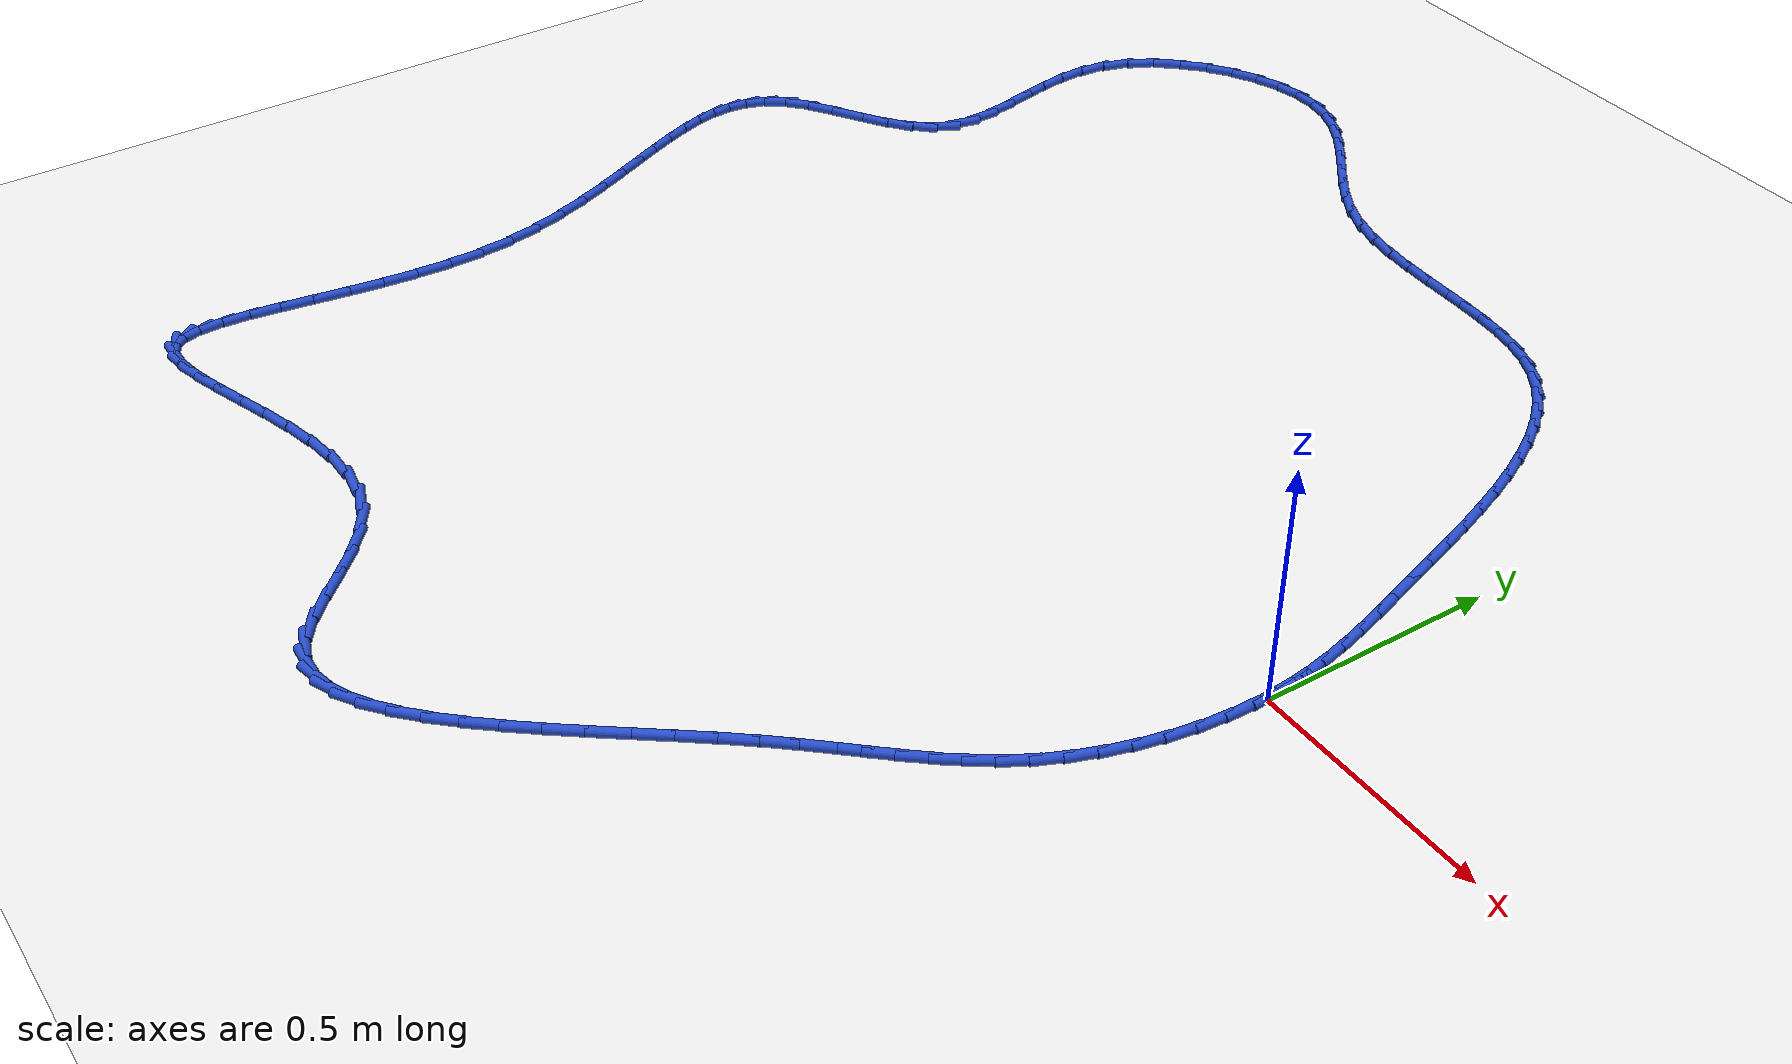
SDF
<sdf version="1.6">
 <world name="default">
  <light name="sun" type="directional">
   <pose>0 0 10 0 -0 0</pose>
   <diffuse>0.8 0.8 0.8 1</diffuse>
   <specular>0.2 0.2 0.2 1</specular>
   <attenuation>
    <range>1000</range>
    <constant>0.9</constant>
    <linear>0.01</linear>
    <quadratic>0.001</quadratic>
   </attenuation>
   <direction>-0.5 0.1 -0.9</direction>
  </light>
  <model name="ground_plane">
   <static>1</static>
   <link name="link">
    <collision name="collision">
     <geometry><plane><normal>0 0 1</normal><size>100 100</size></plane></geometry>
     <surface><friction><ode><mu>100</mu><mu2>50</mu2></ode></friction></surface>
    </collision>
    <visual name="visual">
     <cast_shadows>0</cast_shadows>
     <geometry><plane><normal>0 0 1</normal><size>100 100</size></plane></geometry>
     <material>
      <script><uri>file://media/materials/scripts/gazebo.material</uri><name>Gazebo/WhiteGlow</name></script>
     </material>
    </visual>
   </link>
  </model>
  <gravity>0 0 -9.8</gravity>
  <magnetic_field>6e-06 2.3e-05 -4.2e-05</magnetic_field>
  <atmosphere type="adiabatic"/>
  <physics name="default_physics" default="0" type="ode">
   <max_step_size>0.001</max_step_size>
   <real_time_factor>1</real_time_factor>
   <real_time_update_rate>1000</real_time_update_rate>
  </physics>
  <scene><ambient>0.4 0.4 0.4 1</ambient><background>0.7 0.7 0.7 1</background><shadows>1</shadows></scene>
  <spherical_coordinates>
   <surface_model>EARTH_WGS84</surface_model>
   <latitude_deg>0</latitude_deg>
   <longitude_deg>0</longitude_deg>
   <elevation>0</elevation>
   <heading_deg>0</heading_deg>
  </spherical_coordinates>
  <model name="line">
   <link name="link_0">
    <pose>4.5102810375396984e-17 -6.938893903907228e-17 0.01 0 1.57 -1.5004712339174642</pose>
    <collision name="collision">
     <geometry><cylinder><radius>0.01</radius><length>0.08</length></cylinder></geometry>
    </collision>
    <visual name="visual">
     <material>
      <script><name>Gazebo/Blue</name><uri>file://media/materials/scripts/gazebo.material</uri></script>
     </material>
     <geometry><cylinder><radius>0.01</radius><length>0.08</length></cylinder></geometry>
    </visual>
   </link>
   <link name="link_1">
    <pose>-0.004037575416281745 0.05731833337059254 0.01 0 1.57 -1.4348186650927535</pose>
    <collision name="collision">
     <geometry><cylinder><radius>0.01</radius><length>0.08</length></cylinder></geometry>
    </collision>
    <visual name="visual">
     <material>
      <script><name>Gazebo/Blue</name><uri>file://media/materials/scripts/gazebo.material</uri></script>
     </material>
     <geometry><cylinder><radius>0.01</radius><length>0.08</length></cylinder></geometry>
    </visual>
   </link>
   <link name="link_2">
    <pose>-0.01175211621200765 0.11370211652022898 0.01 0 1.57 -1.3787049932847433</pose>
    <collision name="collision">
     <geometry><cylinder><radius>0.01</radius><length>0.08</length></cylinder></geometry>
    </collision>
    <visual name="visual">
     <material>
      <script><name>Gazebo/Blue</name><uri>file://media/materials/scripts/gazebo.material</uri></script>
     </material>
     <geometry><cylinder><radius>0.01</radius><length>0.08</length></cylinder></geometry>
    </visual>
   </link>
   <link name="link_3">
    <pose>-0.022615047114090035 0.1695557052910629 0.01 0 1.57 -1.3334182568257678</pose>
    <collision name="collision">
     <geometry><cylinder><radius>0.01</radius><length>0.08</length></cylinder></geometry>
    </collision>
    <visual name="visual">
     <material>
      <script><name>Gazebo/Blue</name><uri>file://media/materials/scripts/gazebo.material</uri></script>
     </material>
     <geometry><cylinder><radius>0.01</radius><length>0.08</length></cylinder></geometry>
    </visual>
   </link>
   <link name="link_4">
    <pose>-0.03609779284944128 0.22528345552524812 0.01 0 1.57 -1.2995728628402556</pose>
    <collision name="collision">
     <geometry><cylinder><radius>0.01</radius><length>0.08</length></cylinder></geometry>
    </collision>
    <visual name="visual">
     <material>
      <script><name>Gazebo/Blue</name><uri>file://media/materials/scripts/gazebo.material</uri></script>
     </material>
     <geometry><cylinder><radius>0.01</radius><length>0.08</length></cylinder></geometry>
    </visual>
   </link>
   <link name="link_5">
    <pose>-0.05167177814497375 0.28128972306493855 0.01 0 1.57 -1.2772384988308771</pose>
    <collision name="collision">
     <geometry><cylinder><radius>0.01</radius><length>0.08</length></cylinder></geometry>
    </collision>
    <visual name="visual">
     <material>
      <script><name>Gazebo/Blue</name><uri>file://media/materials/scripts/gazebo.material</uri></script>
     </material>
     <geometry><cylinder><radius>0.01</radius><length>0.08</length></cylinder></geometry>
    </visual>
   </link>
   <link name="link_6">
    <pose>-0.06880842772759982 0.3379788637522878 0.01 0 1.57 -1.2660893254949797</pose>
    <collision name="collision">
     <geometry><cylinder><radius>0.01</radius><length>0.08</length></cylinder></geometry>
    </collision>
    <visual name="visual">
     <material>
      <script><name>Gazebo/Blue</name><uri>file://media/materials/scripts/gazebo.material</uri></script>
     </material>
     <geometry><cylinder><radius>0.01</radius><length>0.08</length></cylinder></geometry>
    </visual>
   </link>
   <link name="link_7">
    <pose>-0.08697916632423186 0.39575523342944985 0.01 0 1.57 -1.2653944081947126</pose>
    <collision name="collision">
     <geometry><cylinder><radius>0.01</radius><length>0.08</length></cylinder></geometry>
    </collision>
    <visual name="visual">
     <material>
      <script><name>Gazebo/Blue</name><uri>file://media/materials/scripts/gazebo.material</uri></script>
     </material>
     <geometry><cylinder><radius>0.01</radius><length>0.08</length></cylinder></geometry>
    </visual>
   </link>
   <link name="link_8">
    <pose>-0.10566166746171395 0.45501490058101823 0.01 0 1.57 -1.267503994169695</pose>
    <collision name="collision">
     <geometry><cylinder><radius>0.01</radius><length>0.08</length></cylinder></geometry>
    </collision>
    <visual name="visual">
     <material>
      <script><name>Gazebo/Blue</name><uri>file://media/materials/scripts/gazebo.material</uri></script>
     </material>
     <geometry><cylinder><radius>0.01</radius><length>0.08</length></cylinder></geometry>
    </visual>
   </link>
   <link name="link_9">
    <pose>-0.12465964398622445 0.5157215299584679 0.01 0 1.57 -1.2622437780268578</pose>
    <collision name="collision">
     <geometry><cylinder><radius>0.01</radius><length>0.08</length></cylinder></geometry>
    </collision>
    <visual name="visual">
     <material>
      <script><name>Gazebo/Blue</name><uri>file://media/materials/scripts/gazebo.material</uri></script>
     </material>
     <geometry><cylinder><radius>0.01</radius><length>0.08</length></cylinder></geometry>
    </visual>
   </link>
   <link name="link_10">
    <pose>-0.1442559000347422 0.5772034001792652 0.01 0 1.57 -1.2489859484521901</pose>
    <collision name="collision">
     <geometry><cylinder><radius>0.01</radius><length>0.08</length></cylinder></geometry>
    </collision>
    <visual name="visual">
     <material>
      <script><name>Gazebo/Blue</name><uri>file://media/materials/scripts/gazebo.material</uri></script>
     </material>
     <geometry><cylinder><radius>0.01</radius><length>0.08</length></cylinder></geometry>
    </visual>
   </link>
   <link name="link_11">
    <pose>-0.16477152747685883 0.6387380114500136 0.01 0 1.57 -1.2275007552103896</pose>
    <collision name="collision">
     <geometry><cylinder><radius>0.01</radius><length>0.08</length></cylinder></geometry>
    </collision>
    <visual name="visual">
     <material>
      <script><name>Gazebo/Blue</name><uri>file://media/materials/scripts/gazebo.material</uri></script>
     </material>
     <geometry><cylinder><radius>0.01</radius><length>0.08</length></cylinder></geometry>
    </visual>
   </link>
   <link name="link_12">
    <pose>-0.18652761818216598 0.6996028639773169 0.01 0 1.57 -1.1971415014831155</pose>
    <collision name="collision">
     <geometry><cylinder><radius>0.01</radius><length>0.08</length></cylinder></geometry>
    </collision>
    <visual name="visual">
     <material>
      <script><name>Gazebo/Blue</name><uri>file://media/materials/scripts/gazebo.material</uri></script>
     </material>
     <geometry><cylinder><radius>0.01</radius><length>0.08</length></cylinder></geometry>
    </visual>
   </link>
   <link name="link_13">
    <pose>-0.20984526402025536 0.7590754579677793 0.01 0 1.57 -1.156832286936047</pose>
    <collision name="collision">
     <geometry><cylinder><radius>0.01</radius><length>0.08</length></cylinder></geometry>
    </collision>
    <visual name="visual">
     <material>
      <script><name>Gazebo/Blue</name><uri>file://media/materials/scripts/gazebo.material</uri></script>
     </material>
     <geometry><cylinder><radius>0.01</radius><length>0.08</length></cylinder></geometry>
    </visual>
   </link>
   <link name="link_14">
    <pose>-0.2350455568607184 0.8164332936280038 0.01 0 1.57 -1.1050417511093311</pose>
    <collision name="collision">
     <geometry><cylinder><radius>0.01</radius><length>0.08</length></cylinder></geometry>
    </collision>
    <visual name="visual">
     <material>
      <script><name>Gazebo/Blue</name><uri>file://media/materials/scripts/gazebo.material</uri></script>
     </material>
     <geometry><cylinder><radius>0.01</radius><length>0.08</length></cylinder></geometry>
    </visual>
   </link>
   <link name="link_15">
    <pose>-0.2624495885731468 0.8709538711645946 0.01 0 1.57 -1.039773630951853</pose>
    <collision name="collision">
     <geometry><cylinder><radius>0.01</radius><length>0.08</length></cylinder></geometry>
    </collision>
    <visual name="visual">
     <material>
      <script><name>Gazebo/Blue</name><uri>file://media/materials/scripts/gazebo.material</uri></script>
     </material>
     <geometry><cylinder><radius>0.01</radius><length>0.08</length></cylinder></geometry>
    </visual>
   </link>
   <link name="link_16">
    <pose>-0.2923784510271322 0.9219146907841551 0.01 0 1.57 -0.9586370048366245</pose>
    <collision name="collision">
     <geometry><cylinder><radius>0.01</radius><length>0.08</length></cylinder></geometry>
    </collision>
    <visual name="visual">
     <material>
      <script><name>Gazebo/Blue</name><uri>file://media/materials/scripts/gazebo.material</uri></script>
     </material>
     <geometry><cylinder><radius>0.01</radius><length>0.08</length></cylinder></geometry>
    </visual>
   </link>
   <link name="link_17">
    <pose>-0.3251532360922663 0.9685932526932897 0.01 0 1.57 -0.8591155314883006</pose>
    <collision name="collision">
     <geometry><cylinder><radius>0.01</radius><length>0.08</length></cylinder></geometry>
    </collision>
    <visual name="visual">
     <material>
      <script><name>Gazebo/Blue</name><uri>file://media/materials/scripts/gazebo.material</uri></script>
     </material>
     <geometry><cylinder><radius>0.01</radius><length>0.08</length></cylinder></geometry>
    </visual>
   </link>
   <link name="link_18">
    <pose>-0.3610950356381406 1.0102670570986017 0.01 0 1.57 -0.7392181946435298</pose>
    <collision name="collision">
     <geometry><cylinder><radius>0.01</radius><length>0.08</length></cylinder></geometry>
    </collision>
    <visual name="visual">
     <material>
      <script><name>Gazebo/Blue</name><uri>file://media/materials/scripts/gazebo.material</uri></script>
     </material>
     <geometry><cylinder><radius>0.01</radius><length>0.08</length></cylinder></geometry>
    </visual>
   </link>
   <link name="link_19">
    <pose>-0.40052494153434676 1.0462136042066947 0.01 0 1.57 -0.598664868687921</pose>
    <collision name="collision">
     <geometry><cylinder><radius>0.01</radius><length>0.08</length></cylinder></geometry>
    </collision>
    <visual name="visual">
     <material>
      <script><name>Gazebo/Blue</name><uri>file://media/materials/scripts/gazebo.material</uri></script>
     </material>
     <geometry><cylinder><radius>0.01</radius><length>0.08</length></cylinder></geometry>
    </visual>
   </link>
   <link name="link_20">
    <pose>-0.44376404565047645 1.0757103942241728 0.01 0 1.57 -0.44076989092278057</pose>
    <collision name="collision">
     <geometry><cylinder><radius>0.01</radius><length>0.08</length></cylinder></geometry>
    </collision>
    <visual name="visual">
     <material>
      <script><name>Gazebo/Blue</name><uri>file://media/materials/scripts/gazebo.material</uri></script>
     </material>
     <geometry><cylinder><radius>0.01</radius><length>0.08</length></cylinder></geometry>
    </visual>
   </link>
   <link name="link_21">
    <pose>-0.49112551370021873 1.0980518119375509 0.01 0 1.57 -0.28991057319260055</pose>
    <collision name="collision">
     <geometry><cylinder><radius>0.01</radius><length>0.08</length></cylinder></geometry>
    </collision>
    <visual name="visual">
     <material>
      <script><name>Gazebo/Blue</name><uri>file://media/materials/scripts/gazebo.material</uri></script>
     </material>
     <geometry><cylinder><radius>0.01</radius><length>0.08</length></cylinder></geometry>
    </visual>
   </link>
   <link name="link_22">
    <pose>-0.5425225149336386 1.113384328862062 0.01 0 1.57 -0.17540187897770868</pose>
    <collision name="collision">
     <geometry><cylinder><radius>0.01</radius><length>0.08</length></cylinder></geometry>
    </collision>
    <visual name="visual">
     <material>
      <script><name>Gazebo/Blue</name><uri>file://media/materials/scripts/gazebo.material</uri></script>
     </material>
     <geometry><cylinder><radius>0.01</radius><length>0.08</length></cylinder></geometry>
    </visual>
   </link>
   <link name="link_23">
    <pose>-0.5972881653668255 1.1230900665937942 0.01 0 1.57 -0.09649198751842684</pose>
    <collision name="collision">
     <geometry><cylinder><radius>0.01</radius><length>0.08</length></cylinder></geometry>
    </collision>
    <visual name="visual">
     <material>
      <script><name>Gazebo/Blue</name><uri>file://media/materials/scripts/gazebo.material</uri></script>
     </material>
     <geometry><cylinder><radius>0.01</radius><length>0.08</length></cylinder></geometry>
    </visual>
   </link>
   <link name="link_24">
    <pose>-0.6547100768377834 1.1286480813514521 0.01 0 1.57 -0.04863188194610277</pose>
    <collision name="collision">
     <geometry><cylinder><radius>0.01</radius><length>0.08</length></cylinder></geometry>
    </collision>
    <visual name="visual">
     <material>
      <script><name>Gazebo/Blue</name><uri>file://media/materials/scripts/gazebo.material</uri></script>
     </material>
     <geometry><cylinder><radius>0.01</radius><length>0.08</length></cylinder></geometry>
    </visual>
   </link>
   <link name="link_25">
    <pose>-0.7140758611845153 1.1315374293537401 0.01 0 1.57 -0.02804238416598587</pose>
    <collision name="collision">
     <geometry><cylinder><radius>0.01</radius><length>0.08</length></cylinder></geometry>
    </collision>
    <visual name="visual">
     <material>
      <script><name>Gazebo/Blue</name><uri>file://media/materials/scripts/gazebo.material</uri></script>
     </material>
     <geometry><cylinder><radius>0.01</radius><length>0.08</length></cylinder></geometry>
    </visual>
   </link>
   <link name="link_26">
    <pose>-0.7746731302450247 1.1332371668193626 0.01 0 1.57 -0.03253598554440818</pose>
    <collision name="collision">
     <geometry><cylinder><radius>0.01</radius><length>0.08</length></cylinder></geometry>
    </collision>
    <visual name="visual">
     <material>
      <script><name>Gazebo/Blue</name><uri>file://media/materials/scripts/gazebo.material</uri></script>
     </material>
     <geometry><cylinder><radius>0.01</radius><length>0.08</length></cylinder></geometry>
    </visual>
   </link>
   <link name="link_27">
    <pose>-0.8357894958573145 1.1352263499670232 0.01 0 1.57 -0.061601138990094215</pose>
    <collision name="collision">
     <geometry><cylinder><radius>0.01</radius><length>0.08</length></cylinder></geometry>
    </collision>
    <visual name="visual">
     <material>
      <script><name>Gazebo/Blue</name><uri>file://media/materials/scripts/gazebo.material</uri></script>
     </material>
     <geometry><cylinder><radius>0.01</radius><length>0.08</length></cylinder></geometry>
    </visual>
   </link>
   <link name="link_28">
    <pose>-0.896712569859389 1.1389840350154266 0.01 0 1.57 -0.11619445598043322</pose>
    <collision name="collision">
     <geometry><cylinder><radius>0.01</radius><length>0.08</length></cylinder></geometry>
    </collision>
    <visual name="visual">
     <material>
      <script><name>Gazebo/Blue</name><uri>file://media/materials/scripts/gazebo.material</uri></script>
     </material>
     <geometry><cylinder><radius>0.01</radius><length>0.08</length></cylinder></geometry>
    </visual>
   </link>
   <link name="link_29">
    <pose>-0.9567299640892505 1.145989278183276 0.01 0 1.57 -0.19825145970880895</pose>
    <collision name="collision">
     <geometry><cylinder><radius>0.01</radius><length>0.08</length></cylinder></geometry>
    </collision>
    <visual name="visual">
     <material>
      <script><name>Gazebo/Blue</name><uri>file://media/materials/scripts/gazebo.material</uri></script>
     </material>
     <geometry><cylinder><radius>0.01</radius><length>0.08</length></cylinder></geometry>
    </visual>
   </link>
   <link name="link_30">
    <pose>-1.0151292903849032 1.1577211356892771 0.01 0 1.57 -0.3096299711926921</pose>
    <collision name="collision">
     <geometry><cylinder><radius>0.01</radius><length>0.08</length></cylinder></geometry>
    </collision>
    <visual name="visual">
     <material>
      <script><name>Gazebo/Blue</name><uri>file://media/materials/scripts/gazebo.material</uri></script>
     </material>
     <geometry><cylinder><radius>0.01</radius><length>0.08</length></cylinder></geometry>
    </visual>
   </link>
   <link name="link_31">
    <pose>-1.0711981605843497 1.1756586637521331 0.01 0 1.57 -0.44812639900255224</pose>
    <collision name="collision">
     <geometry><cylinder><radius>0.01</radius><length>0.08</length></cylinder></geometry>
    </collision>
    <visual name="visual">
     <material>
      <script><name>Gazebo/Blue</name><uri>file://media/materials/scripts/gazebo.material</uri></script>
     </material>
     <geometry><cylinder><radius>0.01</radius><length>0.08</length></cylinder></geometry>
    </visual>
   </link>
   <link name="link_32">
    <pose>-1.1242675440490124 1.2011715767462456 0.01 0 1.57 -0.5729739702102397</pose>
    <collision name="collision">
     <geometry><cylinder><radius>0.01</radius><length>0.08</length></cylinder></geometry>
    </collision>
    <visual name="visual">
     <material>
      <script><name>Gazebo/Blue</name><uri>file://media/materials/scripts/gazebo.material</uri></script>
     </material>
     <geometry><cylinder><radius>0.01</radius><length>0.08</length></cylinder></geometry>
    </visual>
   </link>
   <link name="link_33">
    <pose>-1.1744849264655297 1.2335704446608597 0.01 0 1.57 -0.6511708534500784</pose>
    <collision name="collision">
     <geometry><cylinder><radius>0.01</radius><length>0.08</length></cylinder></geometry>
    </collision>
    <visual name="visual">
     <material>
      <script><name>Gazebo/Blue</name><uri>file://media/materials/scripts/gazebo.material</uri></script>
     </material>
     <geometry><cylinder><radius>0.01</radius><length>0.08</length></cylinder></geometry>
    </visual>
   </link>
   <link name="link_34">
    <pose>-1.222724986803582 1.270331953802234 0.01 0 1.57 -0.6850809463543324</pose>
    <collision name="collision">
     <geometry><cylinder><radius>0.01</radius><length>0.08</length></cylinder></geometry>
    </collision>
    <visual name="visual">
     <material>
      <script><name>Gazebo/Blue</name><uri>file://media/materials/scripts/gazebo.material</uri></script>
     </material>
     <geometry><cylinder><radius>0.01</radius><length>0.08</length></cylinder></geometry>
    </visual>
   </link>
   <link name="link_35">
    <pose>-1.2698878217469465 1.308868690419293 0.01 0 1.57 -0.6765031997794814</pose>
    <collision name="collision">
     <geometry><cylinder><radius>0.01</radius><length>0.08</length></cylinder></geometry>
    </collision>
    <visual name="visual">
     <material>
      <script><name>Gazebo/Blue</name><uri>file://media/materials/scripts/gazebo.material</uri></script>
     </material>
     <geometry><cylinder><radius>0.01</radius><length>0.08</length></cylinder></geometry>
    </visual>
   </link>
   <link name="link_36">
    <pose>-1.3168735279793988 1.3465932407609604 0.01 0 1.57 -0.6236737821942042</pose>
    <collision name="collision">
     <geometry><cylinder><radius>0.01</radius><length>0.08</length></cylinder></geometry>
    </collision>
    <visual name="visual">
     <material>
      <script><name>Gazebo/Blue</name><uri>file://media/materials/scripts/gazebo.material</uri></script>
     </material>
     <geometry><cylinder><radius>0.01</radius><length>0.08</length></cylinder></geometry>
    </visual>
   </link>
   <link name="link_37">
    <pose>-1.3645822021847158 1.3809181910761603 0.01 0 1.57 -0.521410464800418</pose>
    <collision name="collision">
     <geometry><cylinder><radius>0.01</radius><length>0.08</length></cylinder></geometry>
    </collision>
    <visual name="visual">
     <material>
      <script><name>Gazebo/Blue</name><uri>file://media/materials/scripts/gazebo.material</uri></script>
     </material>
     <geometry><cylinder><radius>0.01</radius><length>0.08</length></cylinder></geometry>
    </visual>
   </link>
   <link name="link_38">
    <pose>-1.4139139410466726 1.4092561276138162 0.01 0 1.57 -0.3641349132534551</pose>
    <collision name="collision">
     <geometry><cylinder><radius>0.01</radius><length>0.08</length></cylinder></geometry>
    </collision>
    <visual name="visual">
     <material>
      <script><name>Gazebo/Blue</name><uri>file://media/materials/scripts/gazebo.material</uri></script>
     </material>
     <geometry><cylinder><radius>0.01</radius><length>0.08</length></cylinder></geometry>
    </visual>
   </link>
   <link name="link_39">
    <pose>-1.4657688412490466 1.429019636622853 0.01 0 1.57 -0.15548329075879744</pose>
    <collision name="collision">
     <geometry><cylinder><radius>0.01</radius><length>0.08</length></cylinder></geometry>
    </collision>
    <visual name="visual">
     <material>
      <script><name>Gazebo/Blue</name><uri>file://media/materials/scripts/gazebo.material</uri></script>
     </material>
     <geometry><cylinder><radius>0.01</radius><length>0.08</length></cylinder></geometry>
    </visual>
   </link>
   <link name="link_40">
    <pose>-1.5210052051698437 1.4376778519018694 0.01 0 1.57 0.05685876160451693</pose>
    <collision name="collision">
     <geometry><cylinder><radius>0.01</radius><length>0.08</length></cylinder></geometry>
    </collision>
    <visual name="visual">
     <material>
      <script><name>Gazebo/Blue</name><uri>file://media/materials/scripts/gazebo.material</uri></script>
     </material>
     <geometry><cylinder><radius>0.01</radius><length>0.08</length></cylinder></geometry>
    </visual>
   </link>
   <link name="link_41">
    <pose>-1.5792525831243873 1.4343624044969927 0.01 0 1.57 0.23534725048124602</pose>
    <collision name="collision">
     <geometry><cylinder><radius>0.01</radius><length>0.08</length></cylinder></geometry>
    </collision>
    <visual name="visual">
     <material>
      <script><name>Gazebo/Blue</name><uri>file://media/materials/scripts/gazebo.material</uri></script>
     </material>
     <geometry><cylinder><radius>0.01</radius><length>0.08</length></cylinder></geometry>
    </visual>
   </link>
   <link name="link_42">
    <pose>-1.6387417675344873 1.4200974399969826 0.01 0 1.57 0.38828807610979277</pose>
    <collision name="collision">
     <geometry><cylinder><radius>0.01</radius><length>0.08</length></cylinder></geometry>
    </collision>
    <visual name="visual">
     <material>
      <script><name>Gazebo/Blue</name><uri>file://media/materials/scripts/gazebo.material</uri></script>
     </material>
     <geometry><cylinder><radius>0.01</radius><length>0.08</length></cylinder></geometry>
    </visual>
   </link>
   <link name="link_43">
    <pose>-1.6976275762655018 1.3960098973000252 0.01 0 1.57 0.5262408574784457</pose>
    <collision name="collision">
     <geometry><cylinder><radius>0.01</radius><length>0.08</length></cylinder></geometry>
    </collision>
    <visual name="visual">
     <material>
      <script><name>Gazebo/Blue</name><uri>file://media/materials/scripts/gazebo.material</uri></script>
     </material>
     <geometry><cylinder><radius>0.01</radius><length>0.08</length></cylinder></geometry>
    </visual>
   </link>
   <link name="link_44">
    <pose>-1.754064827182787 1.3632267153043058 0.01 0 1.57 0.6585987127388626</pose>
    <collision name="collision">
     <geometry><cylinder><radius>0.01</radius><length>0.08</length></cylinder></geometry>
    </collision>
    <visual name="visual">
     <material>
      <script><name>Gazebo/Blue</name><uri>file://media/materials/scripts/gazebo.material</uri></script>
     </material>
     <geometry><cylinder><radius>0.01</radius><length>0.08</length></cylinder></geometry>
    </visual>
   </link>
   <link name="link_45">
    <pose>-1.8062083381516991 1.3228748329080111 0.01 0 1.57 0.7939008683935288</pose>
    <collision name="collision">
     <geometry><cylinder><radius>0.01</radius><length>0.08</length></cylinder></geometry>
    </collision>
    <visual name="visual">
     <material>
      <script><name>Gazebo/Blue</name><uri>file://media/materials/scripts/gazebo.material</uri></script>
     </material>
     <geometry><cylinder><radius>0.01</radius><length>0.08</length></cylinder></geometry>
    </visual>
   </link>
   <link name="link_46">
    <pose>-1.8522129270375958 1.2760811890093262 0.01 0 1.57 0.9404526677247441</pose>
    <collision name="collision">
     <geometry><cylinder><radius>0.01</radius><length>0.08</length></cylinder></geometry>
    </collision>
    <visual name="visual">
     <material>
      <script><name>Gazebo/Blue</name><uri>file://media/materials/scripts/gazebo.material</uri></script>
     </material>
     <geometry><cylinder><radius>0.01</radius><length>0.08</length></cylinder></geometry>
    </visual>
   </link>
   <link name="link_47">
    <pose>-1.8902334117058324 1.2239727225064374 0.01 0 1.57 1.106537522813545</pose>
    <collision name="collision">
     <geometry><cylinder><radius>0.01</radius><length>0.08</length></cylinder></geometry>
    </collision>
    <visual name="visual">
     <material>
      <script><name>Gazebo/Blue</name><uri>file://media/materials/scripts/gazebo.material</uri></script>
     </material>
     <geometry><cylinder><radius>0.01</radius><length>0.08</length></cylinder></geometry>
    </visual>
   </link>
   <link name="link_48">
    <pose>-1.918424610021767 1.1676763722975303 0.01 0 1.57 1.2993235630250008</pose>
    <collision name="collision">
     <geometry><cylinder><radius>0.01</radius><length>0.08</length></cylinder></geometry>
    </collision>
    <visual name="visual">
     <material>
      <script><name>Gazebo/Blue</name><uri>file://media/materials/scripts/gazebo.material</uri></script>
     </material>
     <geometry><cylinder><radius>0.01</radius><length>0.08</length></cylinder></geometry>
    </visual>
   </link>
   <link name="link_49">
    <pose>-1.9349464383682597 1.1083188601990959 0.01 0 1.57 1.4987234341206643</pose>
    <collision name="collision">
     <geometry><cylinder><radius>0.01</radius><length>0.08</length></cylinder></geometry>
    </collision>
    <visual name="visual">
     <material>
      <script><name>Gazebo/Blue</name><uri>file://media/materials/scripts/gazebo.material</uri></script>
     </material>
     <geometry><cylinder><radius>0.01</radius><length>0.08</length></cylinder></geometry>
    </visual>
   </link>
   <link name="link_50">
    <pose>-1.9393759477435166 1.0469665700990698 0.01 0 1.57 -1.4950040653635428</pose>
    <collision name="collision">
     <geometry><cylinder><radius>0.01</radius><length>0.08</length></cylinder></geometry>
    </collision>
    <visual name="visual">
     <material>
      <script><name>Gazebo/Blue</name><uri>file://media/materials/scripts/gazebo.material</uri></script>
     </material>
     <geometry><cylinder><radius>0.01</radius><length>0.08</length></cylinder></geometry>
    </visual>
   </link>
   <link name="link_51">
    <pose>-1.9346356775702964 0.9845434436365379 0.01 0 1.57 -1.4045103430950683</pose>
    <collision name="collision">
     <geometry><cylinder><radius>0.01</radius><length>0.08</length></cylinder></geometry>
    </collision>
    <visual name="visual">
     <material>
      <script><name>Gazebo/Blue</name><uri>file://media/materials/scripts/gazebo.material</uri></script>
     </material>
     <geometry><cylinder><radius>0.01</radius><length>0.08</length></cylinder></geometry>
    </visual>
   </link>
   <link name="link_52">
    <pose>-1.9241307403539032 0.9219528757362057 0.01 0 1.57 -1.36574007673455</pose>
    <collision name="collision">
     <geometry><cylinder><radius>0.01</radius><length>0.08</length></cylinder></geometry>
    </collision>
    <visual name="visual">
     <material>
      <script><name>Gazebo/Blue</name><uri>file://media/materials/scripts/gazebo.material</uri></script>
     </material>
     <geometry><cylinder><radius>0.01</radius><length>0.08</length></cylinder></geometry>
    </visual>
   </link>
   <link name="link_53">
    <pose>-1.9112662485996392 0.8600982613227794 0.01 0 1.57 -1.3769821323612723</pose>
    <collision name="collision">
     <geometry><cylinder><radius>0.01</radius><length>0.08</length></cylinder></geometry>
    </collision>
    <visual name="visual">
     <material>
      <script><name>Gazebo/Blue</name><uri>file://media/materials/scripts/gazebo.material</uri></script>
     </material>
     <geometry><cylinder><radius>0.01</radius><length>0.08</length></cylinder></geometry>
    </visual>
   </link>
   <link name="link_54">
    <pose>-1.8994473148128097 0.7998829953209661 0.01 0 1.57 -1.4437243510443445</pose>
    <collision name="collision">
     <geometry><cylinder><radius>0.01</radius><length>0.08</length></cylinder></geometry>
    </collision>
    <visual name="visual">
     <material>
      <script><name>Gazebo/Blue</name><uri>file://media/materials/scripts/gazebo.material</uri></script>
     </material>
     <geometry><cylinder><radius>0.01</radius><length>0.08</length></cylinder></geometry>
    </visual>
   </link>
   <link name="link_55">
    <pose>-1.8920790514987167 0.7422104726554709 0.01 0 1.57 1.5618061177882698</pose>
    <collision name="collision">
     <geometry><cylinder><radius>0.01</radius><length>0.08</length></cylinder></geometry>
    </collision>
    <visual name="visual">
     <material>
      <script><name>Gazebo/Blue</name><uri>file://media/materials/scripts/gazebo.material</uri></script>
     </material>
     <geometry><cylinder><radius>0.01</radius><length>0.08</length></cylinder></geometry>
    </visual>
   </link>
   <link name="link_56">
    <pose>-1.892566571162664 0.6879840882510012 0.01 0 1.57 1.3394646800558065</pose>
    <collision name="collision">
     <geometry><cylinder><radius>0.01</radius><length>0.08</length></cylinder></geometry>
    </collision>
    <visual name="visual">
     <material>
      <script><name>Gazebo/Blue</name><uri>file://media/materials/scripts/gazebo.material</uri></script>
     </material>
     <geometry><cylinder><radius>0.01</radius><length>0.08</length></cylinder></geometry>
    </visual>
   </link>
   <link name="link_57">
    <pose>-1.9043149863099567 0.6381072370322626 0.01 0 1.57 1.040786274864794</pose>
    <collision name="collision">
     <geometry><cylinder><radius>0.01</radius><length>0.08</length></cylinder></geometry>
    </collision>
    <visual name="visual">
     <material>
      <script><name>Gazebo/Blue</name><uri>file://media/materials/scripts/gazebo.material</uri></script>
     </material>
     <geometry><cylinder><radius>0.01</radius><length>0.08</length></cylinder></geometry>
    </visual>
   </link>
   <link name="link_58">
    <pose>-1.9304994852530675 0.5934184927974565 0.01 0 1.57 0.7875707036933844</pose>
    <collision name="collision">
     <geometry><cylinder><radius>0.01</radius><length>0.08</length></cylinder></geometry>
    </collision>
    <visual name="visual">
     <material>
      <script><name>Gazebo/Blue</name><uri>file://media/materials/scripts/gazebo.material</uri></script>
     </material>
     <geometry><cylinder><radius>0.01</radius><length>0.08</length></cylinder></geometry>
    </visual>
   </link>
   <link name="link_59">
    <pose>-1.9701558583655765 0.5535894341097335 0.01 0 1.57 0.6418659208136365</pose>
    <collision name="collision">
     <geometry><cylinder><radius>0.01</radius><length>0.08</length></cylinder></geometry>
    </collision>
    <visual name="visual">
     <material>
      <script><name>Gazebo/Blue</name><uri>file://media/materials/scripts/gazebo.material</uri></script>
     </material>
     <geometry><cylinder><radius>0.01</radius><length>0.08</length></cylinder></geometry>
    </visual>
   </link>
   <link name="link_60">
    <pose>-2.018733128095006 0.5172804439089392 0.01 0 1.57 0.5740225865184843</pose>
    <collision name="collision">
     <geometry><cylinder><radius>0.01</radius><length>0.08</length></cylinder></geometry>
    </collision>
    <visual name="visual">
     <material>
      <script><name>Gazebo/Blue</name><uri>file://media/materials/scripts/gazebo.material</uri></script>
     </material>
     <geometry><cylinder><radius>0.01</radius><length>0.08</length></cylinder></geometry>
    </visual>
   </link>
   <link name="link_61">
    <pose>-2.0715616306568503 0.48311844464880666 0.01 0 1.57 0.5672209846844791</pose>
    <collision name="collision">
     <geometry><cylinder><radius>0.01</radius><length>0.08</length></cylinder></geometry>
    </collision>
    <visual name="visual">
     <material>
      <script><name>Gazebo/Blue</name><uri>file://media/materials/scripts/gazebo.material</uri></script>
     </material>
     <geometry><cylinder><radius>0.01</radius><length>0.08</length></cylinder></geometry>
    </visual>
   </link>
   <link name="link_62">
    <pose>-2.123971702266603 0.4497303587830698 0.01 0 1.57 0.6228450337936121</pose>
    <collision name="collision">
     <geometry><cylinder><radius>0.01</radius><length>0.08</length></cylinder></geometry>
    </collision>
    <visual name="visual">
     <material>
      <script><name>Gazebo/Blue</name><uri>file://media/materials/scripts/gazebo.material</uri></script>
     </material>
     <geometry><cylinder><radius>0.01</radius><length>0.08</length></cylinder></geometry>
    </visual>
   </link>
   <link name="link_63">
    <pose>-2.17129367913976 0.41574310876546167 0.01 0 1.57 0.7631187010094361</pose>
    <collision name="collision">
     <geometry><cylinder><radius>0.01</radius><length>0.08</length></cylinder></geometry>
    </collision>
    <visual name="visual">
     <material>
      <script><name>Gazebo/Blue</name><uri>file://media/materials/scripts/gazebo.material</uri></script>
     </material>
     <geometry><cylinder><radius>0.01</radius><length>0.08</length></cylinder></geometry>
    </visual>
   </link>
   <link name="link_64">
    <pose>-2.2088854138964997 0.37979018072035164 0.01 0 1.57 0.9925573642246486</pose>
    <collision name="collision">
     <geometry><cylinder><radius>0.01</radius><length>0.08</length></cylinder></geometry>
    </collision>
    <visual name="visual">
     <material>
      <script><name>Gazebo/Blue</name><uri>file://media/materials/scripts/gazebo.material</uri></script>
     </material>
     <geometry><cylinder><radius>0.01</radius><length>0.08</length></cylinder></geometry>
    </visual>
   </link>
   <link name="link_65">
    <pose>-2.23419898649164 0.3410046107175579 0.01 0 1.57 1.2460910407652783</pose>
    <collision name="collision">
     <geometry><cylinder><radius>0.01</radius><length>0.08</length></cylinder></geometry>
    </collision>
    <visual name="visual">
     <material>
      <script><name>Gazebo/Blue</name><uri>file://media/materials/scripts/gazebo.material</uri></script>
     </material>
     <geometry><cylinder><radius>0.01</radius><length>0.08</length></cylinder></geometry>
    </visual>
   </link>
   <link name="link_66">
    <pose>-2.2482168544438603 0.2993615592182069 0.01 0 1.57 1.4800525581453596</pose>
    <collision name="collision">
     <geometry><cylinder><radius>0.01</radius><length>0.08</length></cylinder></geometry>
    </collision>
    <visual name="visual">
     <material>
      <script><name>Gazebo/Blue</name><uri>file://media/materials/scripts/gazebo.material</uri></script>
     </material>
     <geometry><cylinder><radius>0.01</radius><length>0.08</length></cylinder></geometry>
    </visual>
   </link>
   <link name="link_67">
    <pose>-2.2522610115860053 0.254917178533936 0.01 0 1.57 -1.4734654494296775</pose>
    <collision name="collision">
     <geometry><cylinder><radius>0.01</radius><length>0.08</length></cylinder></geometry>
    </collision>
    <visual name="visual">
     <material>
      <script><name>Gazebo/Blue</name><uri>file://media/materials/scripts/gazebo.material</uri></script>
     </material>
     <geometry><cylinder><radius>0.01</radius><length>0.08</length></cylinder></geometry>
    </visual>
   </link>
   <link name="link_68">
    <pose>-2.247653451750923 0.20772762097638142 0.01 0 1.57 -1.335887949740576</pose>
    <collision name="collision">
     <geometry><cylinder><radius>0.01</radius><length>0.08</length></cylinder></geometry>
    </collision>
    <visual name="visual">
     <material>
      <script><name>Gazebo/Blue</name><uri>file://media/materials/scripts/gazebo.material</uri></script>
     </material>
     <geometry><cylinder><radius>0.01</radius><length>0.08</length></cylinder></geometry>
    </visual>
   </link>
   <link name="link_69">
    <pose>-2.235716168771457 0.15784903885718057 0.01 0 1.57 -1.2415032483762682</pose>
    <collision name="collision">
     <geometry><cylinder><radius>0.01</radius><length>0.08</length></cylinder></geometry>
    </collision>
    <visual name="visual">
     <material>
      <script><name>Gazebo/Blue</name><uri>file://media/materials/scripts/gazebo.material</uri></script>
     </material>
     <geometry><cylinder><radius>0.01</radius><length>0.08</length></cylinder></geometry>
    </visual>
   </link>
   <link name="link_70">
    <pose>-2.2177711564804556 0.1053375844879695 0.01 0 1.57 -1.1810062492771167</pose>
    <collision name="collision">
     <geometry><cylinder><radius>0.01</radius><length>0.08</length></cylinder></geometry>
    </collision>
    <visual name="visual">
     <material>
      <script><name>Gazebo/Blue</name><uri>file://media/materials/scripts/gazebo.material</uri></script>
     </material>
     <geometry><cylinder><radius>0.01</radius><length>0.08</length></cylinder></geometry>
    </visual>
   </link>
   <link name="link_71">
    <pose>-2.195140408710766 0.05024941018038589 0.01 0 1.57 -1.1469243754719398</pose>
    <collision name="collision">
     <geometry><cylinder><radius>0.01</radius><length>0.08</length></cylinder></geometry>
    </collision>
    <visual name="visual">
     <material>
      <script><name>Gazebo/Blue</name><uri>file://media/materials/scripts/gazebo.material</uri></script>
     </material>
     <geometry><cylinder><radius>0.01</radius><length>0.08</length></cylinder></geometry>
    </visual>
   </link>
   <link name="link_72">
    <pose>-2.169145919295232 -0.007359331753933905 0.01 0 1.57 -1.1341405000539357</pose>
    <collision name="collision">
     <geometry><cylinder><radius>0.01</radius><length>0.08</length></cylinder></geometry>
    </collision>
    <visual name="visual">
     <material>
      <script><name>Gazebo/Blue</name><uri>file://media/materials/scripts/gazebo.material</uri></script>
     </material>
     <geometry><cylinder><radius>0.01</radius><length>0.08</length></cylinder></geometry>
    </visual>
   </link>
   <link name="link_73">
    <pose>-2.1411096820667 -0.06743248900335407 0.01 0 1.57 -1.1394655632209676</pose>
    <collision name="collision">
     <geometry><cylinder><radius>0.01</radius><length>0.08</length></cylinder></geometry>
    </collision>
    <visual name="visual">
     <material>
      <script><name>Gazebo/Blue</name><uri>file://media/materials/scripts/gazebo.material</uri></script>
     </material>
     <geometry><cylinder><radius>0.01</radius><length>0.08</length></cylinder></geometry>
    </visual>
   </link>
   <link name="link_74">
    <pose>-2.1123536908580194 -0.12991390925623592 0.01 0 1.57 -1.1611197248287282</pose>
    <collision name="collision">
     <geometry><cylinder><radius>0.01</radius><length>0.08</length></cylinder></geometry>
    </collision>
    <visual name="visual">
     <material>
      <script><name>Gazebo/Blue</name><uri>file://media/materials/scripts/gazebo.material</uri></script>
     </material>
     <geometry><cylinder><radius>0.01</radius><length>0.08</length></cylinder></geometry>
    </visual>
   </link>
   <link name="link_75">
    <pose>-2.084199939502034 -0.1947474402009436 0.01 0 1.57 -1.1983066249727965</pose>
    <collision name="collision">
     <geometry><cylinder><radius>0.01</radius><length>0.08</length></cylinder></geometry>
    </collision>
    <visual name="visual">
     <material>
      <script><name>Gazebo/Blue</name><uri>file://media/materials/scripts/gazebo.material</uri></script>
     </material>
     <geometry><cylinder><radius>0.01</radius><length>0.08</length></cylinder></geometry>
    </visual>
   </link>
   <link name="link_76">
    <pose>-2.05797042183159 -0.2618769295258402 0.01 0 1.57 -1.2508607463985284</pose>
    <collision name="collision">
     <geometry><cylinder><radius>0.01</radius><length>0.08</length></cylinder></geometry>
    </collision>
    <visual name="visual">
     <material>
      <script><name>Gazebo/Blue</name><uri>file://media/materials/scripts/gazebo.material</uri></script>
     </material>
     <geometry><cylinder><radius>0.01</radius><length>0.08</length></cylinder></geometry>
    </visual>
   </link>
   <link name="link_77">
    <pose>-2.034987131679535 -0.3312462249192889 0.01 0 1.57 -1.318900045171862</pose>
    <collision name="collision">
     <geometry><cylinder><radius>0.01</radius><length>0.08</length></cylinder></geometry>
    </collision>
    <visual name="visual">
     <material>
      <script><name>Gazebo/Blue</name><uri>file://media/materials/scripts/gazebo.material</uri></script>
     </material>
     <geometry><cylinder><radius>0.01</radius><length>0.08</length></cylinder></geometry>
    </visual>
   </link>
   <link name="link_78">
    <pose>-2.0165720628787147 -0.4027991740696544 0.01 0 1.57 -1.4024170255771824</pose>
    <collision name="collision">
     <geometry><cylinder><radius>0.01</radius><length>0.08</length></cylinder></geometry>
    </collision>
    <visual name="visual">
     <material>
      <script><name>Gazebo/Blue</name><uri>file://media/materials/scripts/gazebo.material</uri></script>
     </material>
     <geometry><cylinder><radius>0.01</radius><length>0.08</length></cylinder></geometry>
    </visual>
   </link>
   <link name="link_79">
    <pose>-2.0040472092619743 -0.47647962466529714 0.01 0 1.57 -1.4961747887606651</pose>
    <collision name="collision">
     <geometry><cylinder><radius>0.01</radius><length>0.08</length></cylinder></geometry>
    </collision>
    <visual name="visual">
     <material>
      <script><name>Gazebo/Blue</name><uri>file://media/materials/scripts/gazebo.material</uri></script>
     </material>
     <geometry><cylinder><radius>0.01</radius><length>0.08</length></cylinder></geometry>
    </visual>
   </link>
   <link name="link_80">
    <pose>-1.998394159187394 -0.552095238607472 0.01 0 1.57 1.5657141441001043</pose>
    <collision name="collision">
     <geometry><cylinder><radius>0.01</radius><length>0.08</length></cylinder></geometry>
    </collision>
    <visual name="visual">
     <material>
      <script><name>Gazebo/Blue</name><uri>file://media/materials/scripts/gazebo.material</uri></script>
     </material>
     <geometry><cylinder><radius>0.01</radius><length>0.08</length></cylinder></geometry>
    </visual>
   </link>
   <link name="link_81">
    <pose>-1.9987836303533257 -0.6287292040024194 0.01 0 1.57 1.505487988246205</pose>
    <collision name="collision">
     <geometry><cylinder><radius>0.01</radius><length>0.08</length></cylinder></geometry>
    </collision>
    <visual name="visual">
     <material>
      <script><name>Gazebo/Blue</name><uri>file://media/materials/scripts/gazebo.material</uri></script>
     </material>
     <geometry><cylinder><radius>0.01</radius><length>0.08</length></cylinder></geometry>
    </visual>
   </link>
   <link name="link_82">
    <pose>-2.0037865420334295 -0.7052247480079566 0.01 0 1.57 1.462355548502805</pose>
    <collision name="collision">
     <geometry><cylinder><radius>0.01</radius><length>0.08</length></cylinder></geometry>
    </collision>
    <visual name="visual">
     <material>
      <script><name>Gazebo/Blue</name><uri>file://media/materials/scripts/gazebo.material</uri></script>
     </material>
     <geometry><cylinder><radius>0.01</radius><length>0.08</length></cylinder></geometry>
    </visual>
   </link>
   <link name="link_83">
    <pose>-2.0119734258110737 -0.7804249426789062 0.01 0 1.57 1.4349822985715075</pose>
    <collision name="collision">
     <geometry><cylinder><radius>0.01</radius><length>0.08</length></cylinder></geometry>
    </collision>
    <visual name="visual">
     <material>
      <script><name>Gazebo/Blue</name><uri>file://media/materials/scripts/gazebo.material</uri></script>
     </material>
     <geometry><cylinder><radius>0.01</radius><length>0.08</length></cylinder></geometry>
    </visual>
   </link>
   <link name="link_84">
    <pose>-2.0219148132696287 -0.8531728600700947 0.01 0 1.57 1.4233832606543892</pose>
    <collision name="collision">
     <geometry><cylinder><radius>0.01</radius><length>0.08</length></cylinder></geometry>
    </collision>
    <visual name="visual">
     <material>
      <script><name>Gazebo/Blue</name><uri>file://media/materials/scripts/gazebo.material</uri></script>
     </material>
     <geometry><cylinder><radius>0.01</radius><length>0.08</length></cylinder></geometry>
    </visual>
   </link>
   <link name="link_85">
    <pose>-2.0321812359924643 -0.922311572236348 0.01 0 1.57 1.4294183403318101</pose>
    <collision name="collision">
     <geometry><cylinder><radius>0.01</radius><length>0.08</length></cylinder></geometry>
    </collision>
    <visual name="visual">
     <material>
      <script><name>Gazebo/Blue</name><uri>file://media/materials/scripts/gazebo.material</uri></script>
     </material>
     <geometry><cylinder><radius>0.01</radius><length>0.08</length></cylinder></geometry>
    </visual>
   </link>
   <link name="link_86">
    <pose>-2.0413432255629504 -0.986684151232491 0.01 0 1.57 1.4578801767955685</pose>
    <collision name="collision">
     <geometry><cylinder><radius>0.01</radius><length>0.08</length></cylinder></geometry>
    </collision>
    <visual name="visual">
     <material>
      <script><name>Gazebo/Blue</name><uri>file://media/materials/scripts/gazebo.material</uri></script>
     </material>
     <geometry><cylinder><radius>0.01</radius><length>0.08</length></cylinder></geometry>
    </visual>
   </link>
   <link name="link_87">
    <pose>-2.047971313564455 -1.0451336691133495 0.01 0 1.57 1.5189692651212758</pose>
    <collision name="collision">
     <geometry><cylinder><radius>0.01</radius><length>0.08</length></cylinder></geometry>
    </collision>
    <visual name="visual">
     <material>
      <script><name>Gazebo/Blue</name><uri>file://media/materials/scripts/gazebo.material</uri></script>
     </material>
     <geometry><cylinder><radius>0.01</radius><length>0.08</length></cylinder></geometry>
    </visual>
   </link>
   <link name="link_88">
    <pose>-2.050636031580349 -1.0965031979337472 0.01 0 1.57 -1.5076308698504028</pose>
    <collision name="collision">
     <geometry><cylinder><radius>0.01</radius><length>0.08</length></cylinder></geometry>
    </collision>
    <visual name="visual">
     <material>
      <script><name>Gazebo/Blue</name><uri>file://media/materials/scripts/gazebo.material</uri></script>
     </material>
     <geometry><cylinder><radius>0.01</radius><length>0.08</length></cylinder></geometry>
    </visual>
   </link>
   <link name="link_89">
    <pose>-2.0479079111940015 -1.1396358097485104 0.01 0 1.57 -1.2949432404691255</pose>
    <collision name="collision">
     <geometry><cylinder><radius>0.01</radius><length>0.08</length></cylinder></geometry>
    </collision>
    <visual name="visual">
     <material>
      <script><name>Gazebo/Blue</name><uri>file://media/materials/scripts/gazebo.material</uri></script>
     </material>
     <geometry><cylinder><radius>0.01</radius><length>0.08</length></cylinder></geometry>
    </visual>
   </link>
   <link name="link_90">
    <pose>-2.0383574839887824 -1.1733745766124646 0.01 0 1.57 -0.9160419724431071</pose>
    <collision name="collision">
     <geometry><cylinder><radius>0.01</radius><length>0.08</length></cylinder></geometry>
    </collision>
    <visual name="visual">
     <material>
      <script><name>Gazebo/Blue</name><uri>file://media/materials/scripts/gazebo.material</uri></script>
     </material>
     <geometry><cylinder><radius>0.01</radius><length>0.08</length></cylinder></geometry>
    </visual>
   </link>
   <link name="link_91">
    <pose>-2.0205552815480616 -1.1965625705804352 0.01 0 1.57 -0.39927069895030376</pose>
    <collision name="collision">
     <geometry><cylinder><radius>0.01</radius><length>0.08</length></cylinder></geometry>
    </collision>
    <visual name="visual">
     <material>
      <script><name>Gazebo/Blue</name><uri>file://media/materials/scripts/gazebo.material</uri></script>
     </material>
     <geometry><cylinder><radius>0.01</radius><length>0.08</length></cylinder></geometry>
    </visual>
   </link>
   <link name="link_92">
    <pose>-1.9931426326123498 -1.2081288941791408 0.01 0 1.57 -0.014847775576690255</pose>
    <collision name="collision">
     <geometry><cylinder><radius>0.01</radius><length>0.08</length></cylinder></geometry>
    </collision>
    <visual name="visual">
     <material>
      <script><name>Gazebo/Blue</name><uri>file://media/materials/scripts/gazebo.material</uri></script>
     </material>
     <geometry><cylinder><radius>0.01</radius><length>0.08</length></cylinder></geometry>
    </visual>
   </link>
   <link name="link_93">
    <pose>-1.9561398464917816 -1.2086783436203206 0.01 0 1.57 0.18198586436823372</pose>
    <collision name="collision">
     <geometry><cylinder><radius>0.01</radius><length>0.08</length></cylinder></geometry>
    </collision>
    <visual name="visual">
     <material>
      <script><name>Gazebo/Blue</name><uri>file://media/materials/scripts/gazebo.material</uri></script>
     </material>
     <geometry><cylinder><radius>0.01</radius><length>0.08</length></cylinder></geometry>
    </visual>
   </link>
   <link name="link_94">
    <pose>-1.9108204469783474 -1.2003385818184567 0.01 0 1.57 0.2800348995322928</pose>
    <collision name="collision">
     <geometry><cylinder><radius>0.01</radius><length>0.08</length></cylinder></geometry>
    </collision>
    <visual name="visual">
     <material>
      <script><name>Gazebo/Blue</name><uri>file://media/materials/scripts/gazebo.material</uri></script>
     </material>
     <geometry><cylinder><radius>0.01</radius><length>0.08</length></cylinder></geometry>
    </visual>
   </link>
   <link name="link_95">
    <pose>-1.8585035296682855 -1.1852926491068867 0.01 0 1.57 0.3254283040956408</pose>
    <collision name="collision">
     <geometry><cylinder><radius>0.01</radius><length>0.08</length></cylinder></geometry>
    </collision>
    <visual name="visual">
     <material>
      <script><name>Gazebo/Blue</name><uri>file://media/materials/scripts/gazebo.material</uri></script>
     </material>
     <geometry><cylinder><radius>0.01</radius><length>0.08</length></cylinder></geometry>
    </visual>
   </link>
   <link name="link_96">
    <pose>-1.800508190157837 -1.1657235858189499 0.01 0 1.57 0.33788899911484505</pose>
    <collision name="collision">
     <geometry><cylinder><radius>0.01</radius><length>0.08</length></cylinder></geometry>
    </collision>
    <visual name="visual">
     <material>
      <script><name>Gazebo/Blue</name><uri>file://media/materials/scripts/gazebo.material</uri></script>
     </material>
     <geometry><cylinder><radius>0.01</radius><length>0.08</length></cylinder></geometry>
    </visual>
   </link>
   <link name="link_97">
    <pose>-1.7381535240432426 -1.1438144322879849 0.01 0 1.57 0.3254330573580249</pose>
    <collision name="collision">
     <geometry><cylinder><radius>0.01</radius><length>0.08</length></cylinder></geometry>
    </collision>
    <visual name="visual">
     <material>
      <script><name>Gazebo/Blue</name><uri>file://media/materials/scripts/gazebo.material</uri></script>
     </material>
     <geometry><cylinder><radius>0.01</radius><length>0.08</length></cylinder></geometry>
    </visual>
   </link>
   <link name="link_98">
    <pose>-1.6727586269207408 -1.1217482288473295 0.01 0 1.57 0.2901632192983398</pose>
    <collision name="collision">
     <geometry><cylinder><radius>0.01</radius><length>0.08</length></cylinder></geometry>
    </collision>
    <visual name="visual">
     <material>
      <script><name>Gazebo/Blue</name><uri>file://media/materials/scripts/gazebo.material</uri></script>
     </material>
     <geometry><cylinder><radius>0.01</radius><length>0.08</length></cylinder></geometry>
    </visual>
   </link>
   <link name="link_99">
    <pose>-1.6056425943865724 -1.101708015830323 0.01 0 1.57 0.23031272489078133</pose>
    <collision name="collision">
     <geometry><cylinder><radius>0.01</radius><length>0.08</length></cylinder></geometry>
    </collision>
    <visual name="visual">
     <material>
      <script><name>Gazebo/Blue</name><uri>file://media/materials/scripts/gazebo.material</uri></script>
     </material>
     <geometry><cylinder><radius>0.01</radius><length>0.08</length></cylinder></geometry>
    </visual>
   </link>
   <link name="link_100">
    <pose>-1.538124522036976 -1.0858768335703026 0.01 0 1.57 0.14078858756525214</pose>
    <collision name="collision">
     <geometry><cylinder><radius>0.01</radius><length>0.08</length></cylinder></geometry>
    </collision>
    <visual name="visual">
     <material>
      <script><name>Gazebo/Blue</name><uri>file://media/materials/scripts/gazebo.material</uri></script>
     </material>
     <geometry><cylinder><radius>0.01</radius><length>0.08</length></cylinder></geometry>
    </visual>
   </link>
   <link name="link_101">
    <pose>-1.4715235054681937 -1.0764377224006079 0.01 0 1.57 0.013422662418439486</pose>
    <collision name="collision">
     <geometry><cylinder><radius>0.01</radius><length>0.08</length></cylinder></geometry>
    </collision>
    <visual name="visual">
     <material>
      <script><name>Gazebo/Blue</name><uri>file://media/materials/scripts/gazebo.material</uri></script>
     </material>
     <geometry><cylinder><radius>0.01</radius><length>0.08</length></cylinder></geometry>
    </visual>
   </link>
   <link name="link_102">
    <pose>-1.4071586402764649 -1.0755737226545774 0.01 0 1.57 -0.1612935958398543</pose>
    <collision name="collision">
     <geometry><cylinder><radius>0.01</radius><length>0.08</length></cylinder></geometry>
    </collision>
    <visual name="visual">
     <material>
      <script><name>Gazebo/Blue</name><uri>file://media/materials/scripts/gazebo.material</uri></script>
     </material>
     <geometry><cylinder><radius>0.01</radius><length>0.08</length></cylinder></geometry>
    </visual>
   </link>
   <link name="link_103">
    <pose>-1.346349022058029 -1.0854678746655488 0.01 0 1.57 -0.3832897075455356</pose>
    <collision name="collision">
     <geometry><cylinder><radius>0.01</radius><length>0.08</length></cylinder></geometry>
    </collision>
    <visual name="visual">
     <material>
      <script><name>Gazebo/Blue</name><uri>file://media/materials/scripts/gazebo.material</uri></script>
     </material>
     <geometry><cylinder><radius>0.01</radius><length>0.08</length></cylinder></geometry>
    </visual>
   </link>
   <link name="link_104">
    <pose>-1.2903264238031158 -1.1080579941446016 0.01 0 1.57 -0.5827652554110312</pose>
    <collision name="collision">
     <geometry><cylinder><radius>0.01</radius><length>0.08</length></cylinder></geometry>
    </collision>
    <visual name="visual">
     <material>
      <script><name>Gazebo/Blue</name><uri>file://media/materials/scripts/gazebo.material</uri></script>
     </material>
     <geometry><cylinder><radius>0.01</radius><length>0.08</length></cylinder></geometry>
    </visual>
   </link>
   <link name="link_105">
    <pose>-1.2390925856940835 -1.141827644296358 0.01 0 1.57 -0.7121658562240869</pose>
    <collision name="collision">
     <geometry><cylinder><radius>0.01</radius><length>0.08</length></cylinder></geometry>
    </collision>
    <visual name="visual">
     <material>
      <script><name>Gazebo/Blue</name><uri>file://media/materials/scripts/gazebo.material</uri></script>
     </material>
     <geometry><cylinder><radius>0.01</radius><length>0.08</length></cylinder></geometry>
    </visual>
   </link>
   <link name="link_106">
    <pose>-1.191740061805252 -1.1827071569218497 0.01 0 1.57 -0.779278776670113</pose>
    <collision name="collision">
     <geometry><cylinder><radius>0.01</radius><length>0.08</length></cylinder></geometry>
    </collision>
    <visual name="visual">
     <material>
      <script><name>Gazebo/Blue</name><uri>file://media/materials/scripts/gazebo.material</uri></script>
     </material>
     <geometry><cylinder><radius>0.01</radius><length>0.08</length></cylinder></geometry>
    </visual>
   </link>
   <link name="link_107">
    <pose>-1.1473400962004658 -1.2265670197621517 0.01 0 1.57 -0.7893298609541206</pose>
    <collision name="collision">
     <geometry><cylinder><radius>0.01</radius><length>0.08</length></cylinder></geometry>
    </collision>
    <visual name="visual">
     <material>
      <script><name>Gazebo/Blue</name><uri>file://media/materials/scripts/gazebo.material</uri></script>
     </material>
     <geometry><cylinder><radius>0.01</radius><length>0.08</length></cylinder></geometry>
    </visual>
   </link>
   <link name="link_108">
    <pose>-1.1049639329435696 -1.2692777205583399 0.01 0 1.57 -0.7365368606894972</pose>
    <collision name="collision">
     <geometry><cylinder><radius>0.01</radius><length>0.08</length></cylinder></geometry>
    </collision>
    <visual name="visual">
     <material>
      <script><name>Gazebo/Blue</name><uri>file://media/materials/scripts/gazebo.material</uri></script>
     </material>
     <geometry><cylinder><radius>0.01</radius><length>0.08</length></cylinder></geometry>
    </visual>
   </link>
   <link name="link_109">
    <pose>-1.0636828160984073 -1.3067097470514901 0.01 0 1.57 -0.5982695090122924</pose>
    <collision name="collision">
     <geometry><cylinder><radius>0.01</radius><length>0.08</length></cylinder></geometry>
    </collision>
    <visual name="visual">
     <material>
      <script><name>Gazebo/Blue</name><uri>file://media/materials/scripts/gazebo.material</uri></script>
     </material>
     <geometry><cylinder><radius>0.01</radius><length>0.08</length></cylinder></geometry>
    </visual>
   </link>
   <link name="link_110">
    <pose>-1.0225679897288245 -1.3347335869826762 0.01 0 1.57 -0.34609540625830315</pose>
    <collision name="collision">
     <geometry><cylinder><radius>0.01</radius><length>0.08</length></cylinder></geometry>
    </collision>
    <visual name="visual">
     <material>
      <script><name>Gazebo/Blue</name><uri>file://media/materials/scripts/gazebo.material</uri></script>
     </material>
     <geometry><cylinder><radius>0.01</radius><length>0.08</length></cylinder></geometry>
    </visual>
   </link>
   <link name="link_111">
    <pose>-0.9808018425256739 -1.3497948733858416 0.01 0 1.57 -0.04794052591498494</pose>
    <collision name="collision">
     <geometry><cylinder><radius>0.01</radius><length>0.08</length></cylinder></geometry>
    </collision>
    <visual name="visual">
     <material>
      <script><name>Gazebo/Blue</name><uri>file://media/materials/scripts/gazebo.material</uri></script>
     </material>
     <geometry><cylinder><radius>0.01</radius><length>0.08</length></cylinder></geometry>
    </visual>
   </link>
   <link name="link_112">
    <pose>-0.9382426434096215 -1.3518367482900133 0.01 0 1.57 0.22110773160332825</pose>
    <collision name="collision">
     <geometry><cylinder><radius>0.01</radius><length>0.08</length></cylinder></geometry>
    </collision>
    <visual name="visual">
     <material>
      <script><name>Gazebo/Blue</name><uri>file://media/materials/scripts/gazebo.material</uri></script>
     </material>
     <geometry><cylinder><radius>0.01</radius><length>0.08</length></cylinder></geometry>
    </visual>
   </link>
   <link name="link_113">
    <pose>-0.895002742747252 -1.3421171608503804 0.01 0 1.57 0.4324407453227088</pose>
    <collision name="collision">
     <geometry><cylinder><radius>0.01</radius><length>0.08</length></cylinder></geometry>
    </collision>
    <visual name="visual">
     <material>
      <script><name>Gazebo/Blue</name><uri>file://media/materials/scripts/gazebo.material</uri></script>
     </material>
     <geometry><cylinder><radius>0.01</radius><length>0.08</length></cylinder></geometry>
    </visual>
   </link>
   <link name="link_114">
    <pose>-0.8511949482248954 -1.321896426735967 0.01 0 1.57 0.5872667801583888</pose>
    <collision name="collision">
     <geometry><cylinder><radius>0.01</radius><length>0.08</length></cylinder></geometry>
    </collision>
    <visual name="visual">
     <material>
      <script><name>Gazebo/Blue</name><uri>file://media/materials/scripts/gazebo.material</uri></script>
     </material>
     <geometry><cylinder><radius>0.01</radius><length>0.08</length></cylinder></geometry>
    </visual>
   </link>
   <link name="link_115">
    <pose>-0.8069320675288804 -1.2924348616157968 0.01 0 1.57 0.6983146437871968</pose>
    <collision name="collision">
     <geometry><cylinder><radius>0.01</radius><length>0.08</length></cylinder></geometry>
    </collision>
    <visual name="visual">
     <material>
      <script><name>Gazebo/Blue</name><uri>file://media/materials/scripts/gazebo.material</uri></script>
     </material>
     <geometry><cylinder><radius>0.01</radius><length>0.08</length></cylinder></geometry>
    </visual>
   </link>
   <link name="link_116">
    <pose>-0.7623269083455345 -1.254992781158892 0.01 0 1.57 0.7778435520289986</pose>
    <collision name="collision">
     <geometry><cylinder><radius>0.01</radius><length>0.08</length></cylinder></geometry>
    </collision>
    <visual name="visual">
     <material>
      <script><name>Gazebo/Blue</name><uri>file://media/materials/scripts/gazebo.material</uri></script>
     </material>
     <geometry><cylinder><radius>0.01</radius><length>0.08</length></cylinder></geometry>
    </visual>
   </link>
   <link name="link_117">
    <pose>-0.7174922783611865 -1.2108305010342766 0.01 0 1.57 0.8347468802011556</pose>
    <collision name="collision">
     <geometry><cylinder><radius>0.01</radius><length>0.08</length></cylinder></geometry>
    </collision>
    <visual name="visual">
     <material>
      <script><name>Gazebo/Blue</name><uri>file://media/materials/scripts/gazebo.material</uri></script>
     </material>
     <geometry><cylinder><radius>0.01</radius><length>0.08</length></cylinder></geometry>
    </visual>
   </link>
   <link name="link_118">
    <pose>-0.6725409852621661 -1.1612083369109747 0.01 0 1.57 0.874921987681903</pose>
    <collision name="collision">
     <geometry><cylinder><radius>0.01</radius><length>0.08</length></cylinder></geometry>
    </collision>
    <visual name="visual">
     <material>
      <script><name>Gazebo/Blue</name><uri>file://media/materials/scripts/gazebo.material</uri></script>
     </material>
     <geometry><cylinder><radius>0.01</radius><length>0.08</length></cylinder></geometry>
    </visual>
   </link>
   <link name="link_119">
    <pose>-0.6275858367348012 -1.1073866044580096 0.01 0 1.57 0.9021283271725014</pose>
    <collision name="collision">
     <geometry><cylinder><radius>0.01</radius><length>0.08</length></cylinder></geometry>
    </collision>
    <visual name="visual">
     <material>
      <script><name>Gazebo/Blue</name><uri>file://media/materials/scripts/gazebo.material</uri></script>
     </material>
     <geometry><cylinder><radius>0.01</radius><length>0.08</length></cylinder></geometry>
    </visual>
   </link>
   <link name="link_120">
    <pose>-0.5827396404654205 -1.0506256193444041 0.01 0 1.57 0.9186509998514448</pose>
    <collision name="collision">
     <geometry><cylinder><radius>0.01</radius><length>0.08</length></cylinder></geometry>
    </collision>
    <visual name="visual">
     <material>
      <script><name>Gazebo/Blue</name><uri>file://media/materials/scripts/gazebo.material</uri></script>
     </material>
     <geometry><cylinder><radius>0.01</radius><length>0.08</length></cylinder></geometry>
    </visual>
   </link>
   <link name="link_121">
    <pose>-0.5381152041403526 -0.9921856972391822 0.01 0 1.57 0.9257099939630972</pose>
    <collision name="collision">
     <geometry><cylinder><radius>0.01</radius><length>0.08</length></cylinder></geometry>
    </collision>
    <visual name="visual">
     <material>
      <script><name>Gazebo/Blue</name><uri>file://media/materials/scripts/gazebo.material</uri></script>
     </material>
     <geometry><cylinder><radius>0.01</radius><length>0.08</length></cylinder></geometry>
    </visual>
   </link>
   <link name="link_122">
    <pose>-0.4938253354459252 -0.9333271538113659 0.01 0 1.57 0.9236663976866242</pose>
    <collision name="collision">
     <geometry><cylinder><radius>0.01</radius><length>0.08</length></cylinder></geometry>
    </collision>
    <visual name="visual">
     <material>
      <script><name>Gazebo/Blue</name><uri>file://media/materials/scripts/gazebo.material</uri></script>
     </material>
     <geometry><cylinder><radius>0.01</radius><length>0.08</length></cylinder></geometry>
    </visual>
   </link>
   <link name="link_123">
    <pose>-0.4499828420684688 -0.875310304729981 0.01 0 1.57 0.9120640662868874</pose>
    <collision name="collision">
     <geometry><cylinder><radius>0.01</radius><length>0.08</length></cylinder></geometry>
    </collision>
    <visual name="visual">
     <material>
      <script><name>Gazebo/Blue</name><uri>file://media/materials/scripts/gazebo.material</uri></script>
     </material>
     <geometry><cylinder><radius>0.01</radius><length>0.08</length></cylinder></geometry>
    </visual>
   </link>
   <link name="link_124">
    <pose>-0.406700531694311 -0.8193954656640496 0.01 0 1.57 0.8896079604553487</pose>
    <collision name="collision">
     <geometry><cylinder><radius>0.01</radius><length>0.08</length></cylinder></geometry>
    </collision>
    <visual name="visual">
     <material>
      <script><name>Gazebo/Blue</name><uri>file://media/materials/scripts/gazebo.material</uri></script>
     </material>
     <geometry><cylinder><radius>0.01</radius><length>0.08</length></cylinder></geometry>
    </visual>
   </link>
   <link name="link_125">
    <pose>-0.3640921591071365 -0.7668333367772391 0.01 0 1.57 0.862621307510708</pose>
    <collision name="collision">
     <geometry><cylinder><radius>0.01</radius><length>0.08</length></cylinder></geometry>
    </collision>
    <visual name="visual">
     <material>
      <script><name>Gazebo/Blue</name><uri>file://media/materials/scripts/gazebo.material</uri></script>
     </material>
     <geometry><cylinder><radius>0.01</radius><length>0.08</length></cylinder></geometry>
    </visual>
   </link>
   <link name="link_126">
    <pose>-0.32234891993106174 -0.7180883919693155 0.01 0 1.57 0.8463050386084112</pose>
    <collision name="collision">
     <geometry><cylinder><radius>0.01</radius><length>0.08</length></cylinder></geometry>
    </collision>
    <visual name="visual">
     <material>
      <script><name>Gazebo/Blue</name><uri>file://media/materials/scripts/gazebo.material</uri></script>
     </material>
     <geometry><cylinder><radius>0.01</radius><length>0.08</length></cylinder></geometry>
    </visual>
   </link>
   <link name="link_127">
    <pose>-0.28179569084146905 -0.6722678942303454 0.01 0 1.57 0.8443819533007817</pose>
    <collision name="collision">
     <geometry><cylinder><radius>0.01</radius><length>0.08</length></cylinder></geometry>
    </collision>
    <visual name="visual">
     <material>
      <script><name>Gazebo/Blue</name><uri>file://media/materials/scripts/gazebo.material</uri></script>
     </material>
     <geometry><cylinder><radius>0.01</radius><length>0.08</length></cylinder></geometry>
    </visual>
   </link>
   <link name="link_128">
    <pose>-0.2427706056374013 -0.6283445122103966 0.01 0 1.57 0.8587560472543636</pose>
    <collision name="collision">
     <geometry><cylinder><radius>0.01</radius><length>0.08</length></cylinder></geometry>
    </collision>
    <visual name="visual">
     <material>
      <script><name>Gazebo/Blue</name><uri>file://media/materials/scripts/gazebo.material</uri></script>
     </material>
     <geometry><cylinder><radius>0.01</radius><length>0.08</length></cylinder></geometry>
    </visual>
   </link>
   <link name="link_129">
    <pose>-0.20561179811790167 -0.5852909145595374 0.01 0 1.57 0.8906394605105759</pose>
    <collision name="collision">
     <geometry><cylinder><radius>0.01</radius><length>0.08</length></cylinder></geometry>
    </collision>
    <visual name="visual">
     <material>
      <script><name>Gazebo/Blue</name><uri>file://media/materials/scripts/gazebo.material</uri></script>
     </material>
     <geometry><cylinder><radius>0.01</radius><length>0.08</length></cylinder></geometry>
    </visual>
   </link>
   <link name="link_130">
    <pose>-0.17065740208201358 -0.5420797699278367 0.01 0 1.57 0.9401781034439678</pose>
    <collision name="collision">
     <geometry><cylinder><radius>0.01</radius><length>0.08</length></cylinder></geometry>
    </collision>
    <visual name="visual">
     <material>
      <script><name>Gazebo/Blue</name><uri>file://media/materials/scripts/gazebo.material</uri></script>
     </material>
     <geometry><cylinder><radius>0.01</radius><length>0.08</length></cylinder></geometry>
    </visual>
   </link>
   <link name="link_131">
    <pose>-0.13824555132877966 -0.497683746965362 0.01 0 1.57 1.0060336384114086</pose>
    <collision name="collision">
     <geometry><cylinder><radius>0.01</radius><length>0.08</length></cylinder></geometry>
    </collision>
    <visual name="visual">
     <material>
      <script><name>Gazebo/Blue</name><uri>file://media/materials/scripts/gazebo.material</uri></script>
     </material>
     <geometry><cylinder><radius>0.01</radius><length>0.08</length></cylinder></geometry>
    </visual>
   </link>
   <link name="link_132">
    <pose>-0.10871437965724434 -0.45107551432218335 0.01 0 1.57 1.0843301289852194</pose>
    <collision name="collision">
     <geometry><cylinder><radius>0.01</radius><length>0.08</length></cylinder></geometry>
    </collision>
    <visual name="visual">
     <material>
      <script><name>Gazebo/Blue</name><uri>file://media/materials/scripts/gazebo.material</uri></script>
     </material>
     <geometry><cylinder><radius>0.01</radius><length>0.08</length></cylinder></geometry>
    </visual>
   </link>
   <link name="link_133">
    <pose>-0.08239189456936918 -0.401303154720913 0.01 0 1.57 1.1623692417068021</pose>
    <collision name="collision">
     <geometry><cylinder><radius>0.01</radius><length>0.08</length></cylinder></geometry>
    </collision>
    <visual name="visual">
     <material>
      <script><name>Gazebo/Blue</name><uri>file://media/materials/scripts/gazebo.material</uri></script>
     </material>
     <geometry><cylinder><radius>0.01</radius><length>0.08</length></cylinder></geometry>
    </visual>
   </link>
   <link name="link_134">
    <pose>-0.05947939403357757 -0.3483584010534023 0.01 0 1.57 1.234630278473538</pose>
    <collision name="collision">
     <geometry><cylinder><radius>0.01</radius><length>0.08</length></cylinder></geometry>
    </collision>
    <visual name="visual">
     <material>
      <script><name>Gazebo/Blue</name><uri>file://media/materials/scripts/gazebo.material</uri></script>
     </material>
     <geometry><cylinder><radius>0.01</radius><length>0.08</length></cylinder></geometry>
    </visual>
   </link>
   <link name="link_135">
    <pose>-0.040091945500515584 -0.2928751750067823 0.01 0 1.57 1.302904493142721</pose>
    <collision name="collision">
     <geometry><cylinder><radius>0.01</radius><length>0.08</length></cylinder></geometry>
    </collision>
    <visual name="visual">
     <material>
      <script><name>Gazebo/Blue</name><uri>file://media/materials/scripts/gazebo.material</uri></script>
     </material>
     <geometry><cylinder><radius>0.01</radius><length>0.08</length></cylinder></geometry>
    </visual>
   </link>
   <link name="link_136">
    <pose>-0.02434296374515082 -0.23549970632142447 0.01 0 1.57 1.3689301337485027</pose>
    <collision name="collision">
     <geometry><cylinder><radius>0.01</radius><length>0.08</length></cylinder></geometry>
    </collision>
    <visual name="visual">
     <material>
      <script><name>Gazebo/Blue</name><uri>file://media/materials/scripts/gazebo.material</uri></script>
     </material>
     <geometry><cylinder><radius>0.01</radius><length>0.08</length></cylinder></geometry>
    </visual>
   </link>
   <link name="link_137">
    <pose>-0.012345863542449913 -0.17687822473769768 0.01 0 1.57 1.4343374556465205</pose>
    <collision name="collision">
     <geometry><cylinder><radius>0.01</radius><length>0.08</length></cylinder></geometry>
    </collision>
    <visual name="visual">
     <material>
      <script><name>Gazebo/Blue</name><uri>file://media/materials/scripts/gazebo.material</uri></script>
     </material>
     <geometry><cylinder><radius>0.01</radius><length>0.08</length></cylinder></geometry>
    </visual>
   </link>
   <link name="link_138">
    <pose>-0.0042140596673798094 -0.11765695999597167 0.01 0 1.57 1.5007277740193266</pose>
    <collision name="collision">
     <geometry><cylinder><radius>0.01</radius><length>0.08</length></cylinder></geometry>
    </collision>
    <visual name="visual">
     <material>
      <script><name>Gazebo/Blue</name><uri>file://media/materials/scripts/gazebo.material</uri></script>
     </material>
     <geometry><cylinder><radius>0.01</radius><length>0.08</length></cylinder></geometry>
    </visual>
   </link>
   <link name="link_139">
    <pose>-6.0966894907487496e-05 -0.058482141836616125 0.01 0 1.57 1.5697538397910515</pose>
    <collision name="collision">
     <geometry><cylinder><radius>0.01</radius><length>0.08</length></cylinder></geometry>
    </collision>
    <visual name="visual">
     <material>
      <script><name>Gazebo/Blue</name><uri>file://media/materials/scripts/gazebo.material</uri></script>
     </material>
     <geometry><cylinder><radius>0.01</radius><length>0.08</length></cylinder></geometry>
    </visual>
   </link>
   <link name="link_140">
    <pose>5.898059818321144e-17 1.3877787807814457e-17 0.01 0 1.57 -1.4983935481771544</pose>
    <collision name="collision">
     <geometry><cylinder><radius>0.01</radius><length>0.08</length></cylinder></geometry>
    </collision>
    <visual name="visual">
     <material>
      <script><name>Gazebo/Blue</name><uri>file://media/materials/scripts/gazebo.material</uri></script>
     </material>
     <geometry><cylinder><radius>0.01</radius><length>0.08</length></cylinder></geometry>
    </visual>
   </link>
   <link name="link_141">
    <pose>-0.004144573757624143 0.057143235773505184 0.01 0 1.57 -1.4983935481771546</pose>
    <collision name="collision">
     <geometry><cylinder><radius>0.01</radius><length>0.08</length></cylinder></geometry>
    </collision>
    <visual name="visual">
     <material>
      <script><name>Gazebo/Blue</name><uri>file://media/materials/scripts/gazebo.material</uri></script>
     </material>
     <geometry><cylinder><radius>0.01</radius><length>0.08</length></cylinder></geometry>
    </visual>
   </link>
  </model>
 </world>
</sdf>
